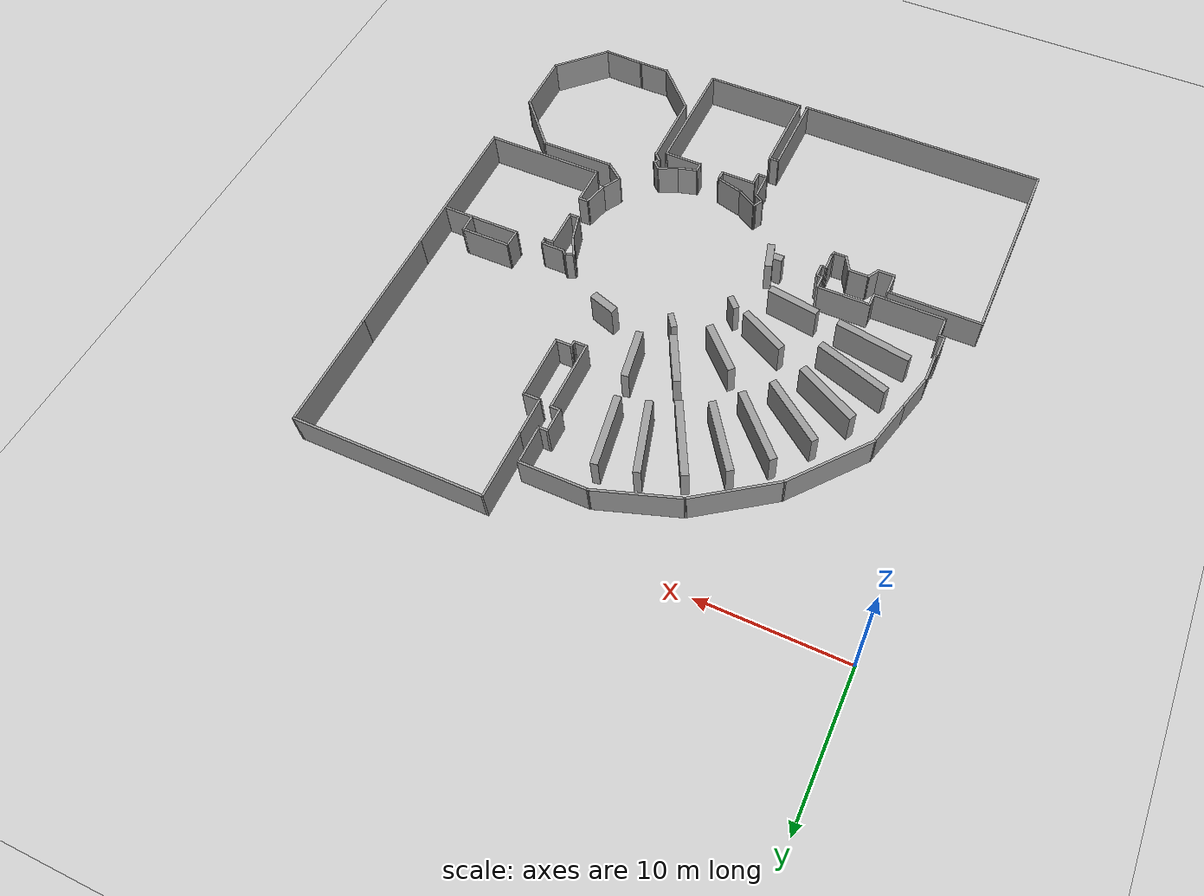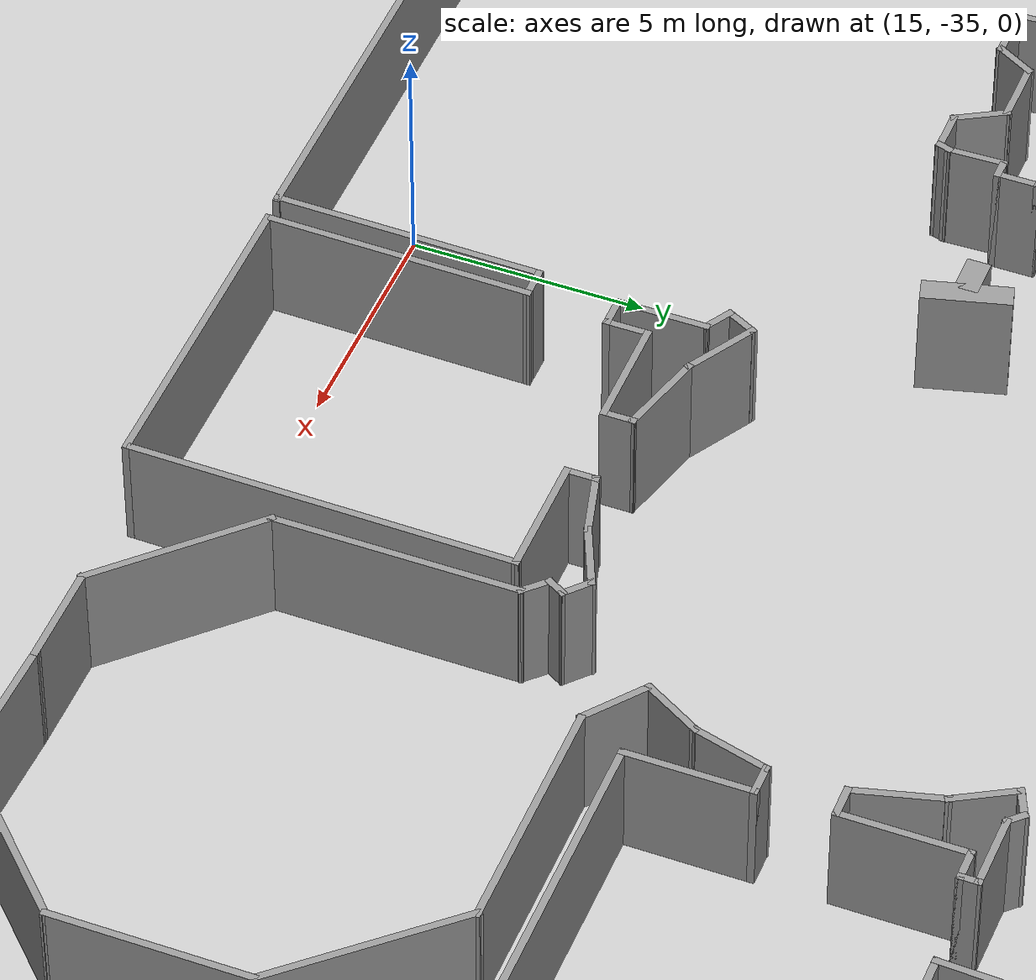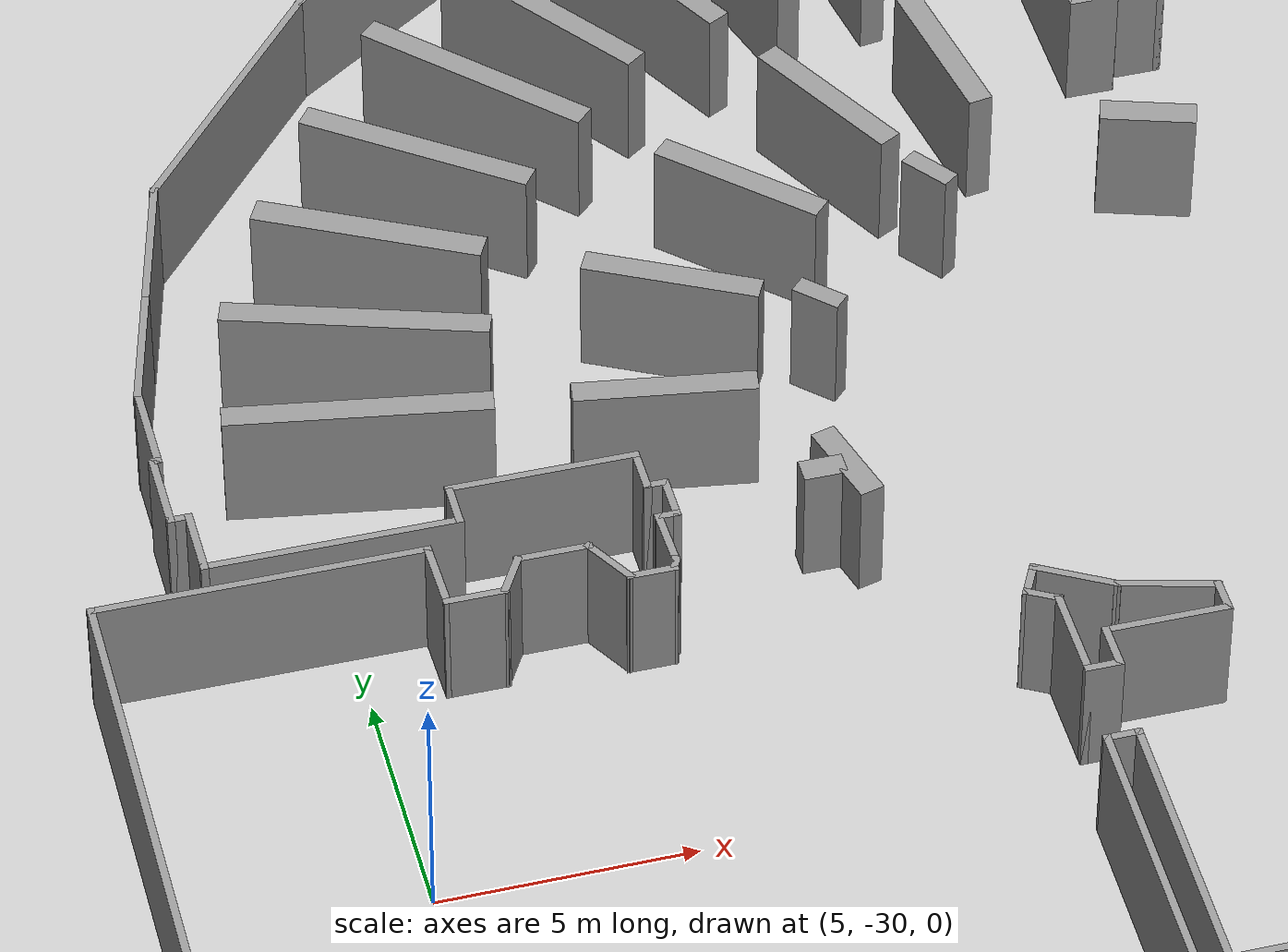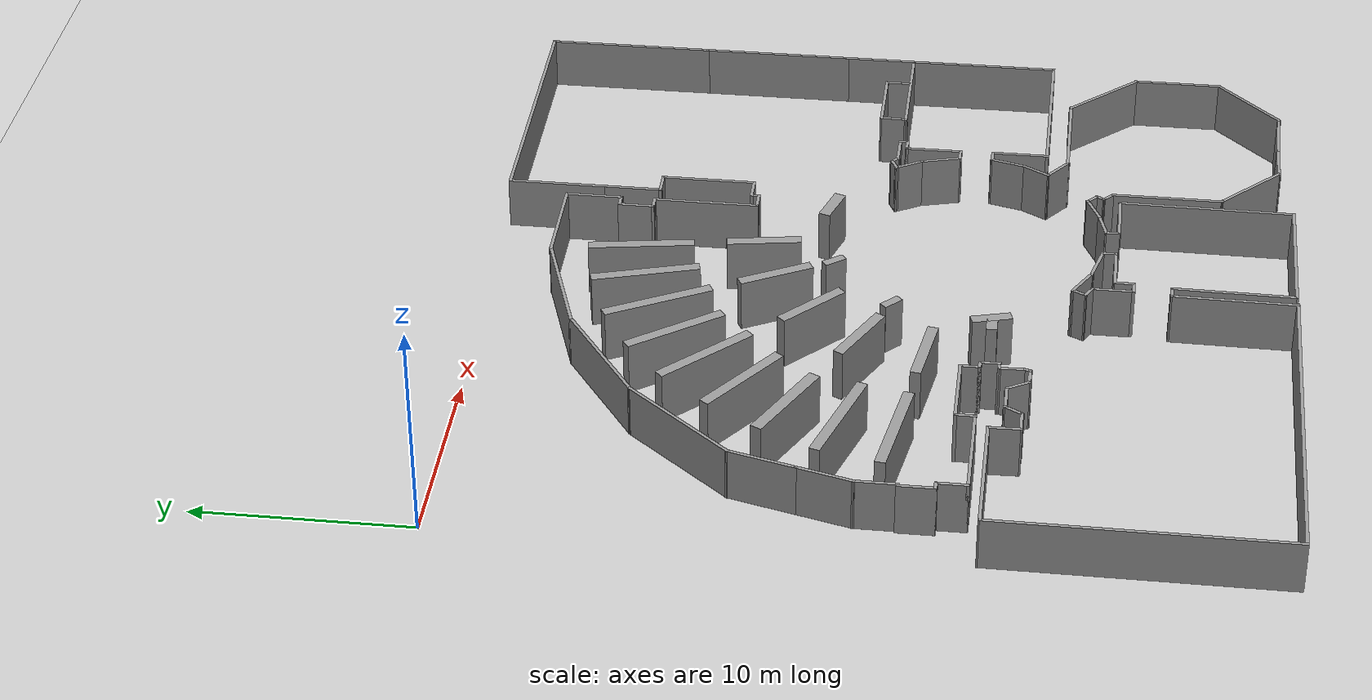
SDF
<sdf version="1.7">
 <world name="default">
  <light name="sun" type="directional">
   <pose>0 0 10 0 -0 0</pose>
   <diffuse>0.8 0.8 0.8 1</diffuse>
   <specular>0.2 0.2 0.2 1</specular>
   <attenuation>
    <range>1000</range>
    <constant>0.9</constant>
    <linear>0.01</linear>
    <quadratic>0.001</quadratic>
   </attenuation>
   <direction>-0.5 0.1 -0.9</direction>
   <spot><inner_angle>0</inner_angle><outer_angle>0</outer_angle><falloff>0</falloff></spot>
  </light>
  <model name="ground_plane">
   <static>1</static>
   <link name="link">
    <collision name="collision">
     <geometry><plane><normal>0 0 1</normal><size>100 100</size></plane></geometry>
     <surface>
      <contact><collide_bitmask>65535</collide_bitmask></contact>
      <friction><ode><mu>100</mu><mu2>50</mu2></ode></friction>
     </surface>
    </collision>
    <visual name="visual">
     <cast_shadows>0</cast_shadows>
     <geometry><plane><normal>0 0 1</normal><size>100 100</size></plane></geometry>
     <material>
      <script><uri>file://media/materials/scripts/gazebo.material</uri><name>Gazebo/Grey</name></script>
     </material>
    </visual>
   </link>
  </model>
  <gravity>0 0 -9.8</gravity>
  <magnetic_field>6e-06 2.3e-05 -4.2e-05</magnetic_field>
  <atmosphere type="adiabatic"/>
  <physics type="ode">
   <max_step_size>0.001</max_step_size>
   <real_time_factor>1</real_time_factor>
   <real_time_update_rate>1000</real_time_update_rate>
  </physics>
  <scene><ambient>0.4 0.4 0.4 1</ambient><background>0.7 0.7 0.7 1</background><shadows>1</shadows></scene>
  <audio><device>default</device></audio>
  <spherical_coordinates>
   <surface_model>EARTH_WGS84</surface_model>
   <latitude_deg>0</latitude_deg>
   <longitude_deg>0</longitude_deg>
   <elevation>0</elevation>
   <heading_deg>0</heading_deg>
  </spherical_coordinates>
  <model name="libraryModel">
   <pose>18.25 -18.5 0 0 -0 0</pose>
   <link name="Wall_1">
    <collision name="Wall_1_Collision">
     <geometry><box><size>6.5 0.15 2.5</size></box></geometry>
     <pose>0 0 1.25 0 -0 0</pose>
    </collision>
    <visual name="Wall_1_Visual">
     <pose>0 0 1.25 0 -0 0</pose>
     <geometry><box><size>6.5 0.15 2.5</size></box></geometry>
     <material>
      <script><uri>file://media/materials/scripts/gazebo.material</uri><name>Gazebo/Grey</name></script>
      <ambient>1 1 1 1</ambient>
     </material>
     <meta><layer>0</layer></meta>
    </visual>
    <pose>-14.9713 -5.1242 0 0 -0 0</pose>
   </link>
   <link name="Wall_10">
    <collision name="Wall_10_Collision">
     <geometry><box><size>1 0.15 2.5</size></box></geometry>
     <pose>0 0 1.25 0 -0 0</pose>
    </collision>
    <visual name="Wall_10_Visual">
     <pose>0 0 1.25 0 -0 0</pose>
     <geometry><box><size>1 0.15 2.5</size></box></geometry>
     <material>
      <script><uri>file://media/materials/scripts/gazebo.material</uri><name>Gazebo/Grey</name></script>
      <ambient>1 1 1 1</ambient>
     </material>
     <meta><layer>0</layer></meta>
    </visual>
    <pose>-7.44635 -4.0992 0 0 -0 1.5708</pose>
   </link>
   <link name="Wall_101">
    <collision name="Wall_101_Collision">
     <geometry><box><size>1.5 0.15 2.5</size></box></geometry>
     <pose>0 0 1.25 0 -0 0</pose>
    </collision>
    <visual name="Wall_101_Visual">
     <pose>0 0 1.25 0 -0 0</pose>
     <geometry><box><size>1.5 0.15 2.5</size></box></geometry>
     <material>
      <script><uri>file://media/materials/scripts/gazebo.material</uri><name>Gazebo/Grey</name></script>
      <ambient>1 1 1 1</ambient>
     </material>
     <meta><layer>0</layer></meta>
    </visual>
    <pose>8.65885 -0.242249 0 0 -0 -1.0472</pose>
   </link>
   <link name="Wall_102">
    <collision name="Wall_102_Collision">
     <geometry><box><size>2 0.15 2.5</size></box></geometry>
     <pose>0 0 1.25 0 -0 0</pose>
    </collision>
    <visual name="Wall_102_Visual">
     <pose>0 0 1.25 0 -0 0</pose>
     <geometry><box><size>2 0.15 2.5</size></box></geometry>
     <material>
      <script><uri>file://media/materials/scripts/gazebo.material</uri><name>Gazebo/Grey</name></script>
      <ambient>1 1 1 1</ambient>
     </material>
     <meta><layer>0</layer></meta>
    </visual>
    <pose>9.23576 -1.7203 0 0 -0 -1.309</pose>
   </link>
   <link name="Wall_103">
    <collision name="Wall_103_Collision">
     <geometry><box><size>0.75 0.15 2.5</size></box></geometry>
     <pose>0 0 1.25 0 -0 0</pose>
    </collision>
    <visual name="Wall_103_Visual">
     <pose>0 0 1.25 0 -0 0</pose>
     <geometry><box><size>0.75 0.15 2.5</size></box></geometry>
     <material>
      <script><uri>file://media/materials/scripts/gazebo.material</uri><name>Gazebo/Grey</name></script>
      <ambient>1 1 1 1</ambient>
     </material>
     <meta><layer>0</layer></meta>
    </visual>
    <pose>9.77517 -2.61378 0 0 -0 0</pose>
   </link>
   <link name="Wall_104">
    <collision name="Wall_104_Collision">
     <geometry><box><size>2.75 0.15 2.5</size></box></geometry>
     <pose>0 0 1.25 0 -0 0</pose>
    </collision>
    <visual name="Wall_104_Visual">
     <pose>0 0 1.25 0 -0 0</pose>
     <geometry><box><size>2.75 0.15 2.5</size></box></geometry>
     <material>
      <script><uri>file://media/materials/scripts/gazebo.material</uri><name>Gazebo/Grey</name></script>
      <ambient>1 1 1 1</ambient>
     </material>
     <meta><layer>0</layer></meta>
    </visual>
    <pose>10.0752 -1.31378 0 0 -0 1.5708</pose>
   </link>
   <link name="Wall_105">
    <collision name="Wall_105_Collision">
     <geometry><box><size>0.75 0.15 2.5</size></box></geometry>
     <pose>0 0 1.25 0 -0 0</pose>
    </collision>
    <visual name="Wall_105_Visual">
     <pose>0 0 1.25 0 -0 0</pose>
     <geometry><box><size>0.75 0.15 2.5</size></box></geometry>
     <material>
      <script><uri>file://media/materials/scripts/gazebo.material</uri><name>Gazebo/Grey</name></script>
      <ambient>1 1 1 1</ambient>
     </material>
     <meta><layer>0</layer></meta>
    </visual>
    <pose>10.3752 -0.013779 0 0 -0 0</pose>
   </link>
   <link name="Wall_106">
    <collision name="Wall_106_Collision">
     <geometry><box><size>0.5 0.15 2.5</size></box></geometry>
     <pose>0 0 1.25 0 -0 0</pose>
    </collision>
    <visual name="Wall_106_Visual">
     <pose>0 0 1.25 0 -0 0</pose>
     <geometry><box><size>0.5 0.15 2.5</size></box></geometry>
     <material>
      <script><uri>file://media/materials/scripts/gazebo.material</uri><name>Gazebo/Grey</name></script>
      <ambient>1 1 1 1</ambient>
     </material>
     <meta><layer>0</layer></meta>
    </visual>
    <pose>10.6752 0.161222 0 0 -0 1.5708</pose>
   </link>
   <link name="Wall_107">
    <collision name="Wall_107_Collision">
     <geometry><box><size>1.71407 0.15 2.5</size></box></geometry>
     <pose>0 0 1.25 0 -0 0</pose>
    </collision>
    <visual name="Wall_107_Visual">
     <pose>0 0 1.25 0 -0 0</pose>
     <geometry><box><size>1.71407 0.15 2.5</size></box></geometry>
     <material>
      <script><uri>file://media/materials/scripts/gazebo.material</uri><name>Gazebo/Grey</name></script>
      <ambient>1 1 1 1</ambient>
     </material>
     <meta><layer>0</layer></meta>
    </visual>
    <pose>9.89314 0.33927 0 0 -0 3.13769</pose>
   </link>
   <link name="Wall_108">
    <collision name="Wall_108_Collision">
     <geometry><box><size>0.5 0.15 2.5</size></box></geometry>
     <pose>0 0 1.25 0 -0 0</pose>
    </collision>
    <visual name="Wall_108_Visual">
     <pose>0 0 1.25 0 -0 0</pose>
     <geometry><box><size>0.5 0.15 2.5</size></box></geometry>
     <material>
      <script><uri>file://media/materials/scripts/gazebo.material</uri><name>Gazebo/Grey</name></script>
      <ambient>1 1 1 1</ambient>
     </material>
     <meta><layer>0</layer></meta>
    </visual>
    <pose>8.98736 0.466062 0 0 -0 2.35619</pose>
   </link>
   <link name="Wall_109">
    <collision name="Wall_109_Collision">
     <geometry><box><size>0.746074 0.15 2.5</size></box></geometry>
     <pose>0 0 1.25 0 -0 0</pose>
    </collision>
    <visual name="Wall_109_Visual">
     <pose>0 0 1.25 0 -0 0</pose>
     <geometry><box><size>0.746074 0.15 2.5</size></box></geometry>
     <material>
      <script><uri>file://media/materials/scripts/gazebo.material</uri><name>Gazebo/Grey</name></script>
      <ambient>1 1 1 1</ambient>
     </material>
     <meta><layer>0</layer></meta>
    </visual>
    <pose>8.59248 0.466062 0 0 -0 -2.71344</pose>
   </link>
   <link name="Wall_11">
    <collision name="Wall_11_Collision">
     <geometry><box><size>3.75 0.15 2.5</size></box></geometry>
     <pose>0 0 1.25 0 -0 0</pose>
    </collision>
    <visual name="Wall_11_Visual">
     <pose>0 0 1.25 0 -0 0</pose>
     <geometry><box><size>3.75 0.15 2.5</size></box></geometry>
     <material>
      <script><uri>file://media/materials/scripts/gazebo.material</uri><name>Gazebo/Grey</name></script>
      <ambient>1 1 1 1</ambient>
     </material>
     <meta><layer>0</layer></meta>
    </visual>
    <pose>-9.24635 -3.6742 0 0 -0 3.14159</pose>
   </link>
   <link name="Wall_111">
    <collision name="Wall_111_Collision">
     <geometry><box><size>5.5 0.15 2.5</size></box></geometry>
     <pose>0 0 1.25 0 -0 0</pose>
    </collision>
    <visual name="Wall_111_Visual">
     <pose>0 0 1.25 0 -0 0</pose>
     <geometry><box><size>5.5 0.15 2.5</size></box></geometry>
     <material>
      <script><uri>file://media/materials/scripts/gazebo.material</uri><name>Gazebo/Grey</name></script>
      <ambient>1 1 1 1</ambient>
     </material>
     <meta><layer>0</layer></meta>
    </visual>
    <pose>15.3789 0.231085 0 0 -0 0</pose>
   </link>
   <link name="Wall_115">
    <collision name="Wall_115_Collision">
     <geometry><box><size>1.8503 0.5 2.5</size></box></geometry>
     <pose>0 0 1.25 0 -0 0</pose>
    </collision>
    <visual name="Wall_115_Visual">
     <pose>0 0 1.25 0 -0 0</pose>
     <geometry><box><size>1.8503 0.5 2.5</size></box></geometry>
     <material>
      <script><uri>file://media/materials/scripts/gazebo.material</uri><name>Gazebo/Grey</name></script>
      <ambient>1 1 1 1</ambient>
     </material>
     <meta><layer>0</layer></meta>
    </visual>
    <pose>-3.6461 -4.83761 0 0 -0 1.83302</pose>
   </link>
   <link name="Wall_117">
    <collision name="Wall_117_Collision">
     <geometry><box><size>0.849678 0.5 2.5</size></box></geometry>
     <pose>0 0 1.25 0 -0 0</pose>
    </collision>
    <visual name="Wall_117_Visual">
     <pose>0 0 1.25 0 -0 0</pose>
     <geometry><box><size>0.849678 0.5 2.5</size></box></geometry>
     <material>
      <script><uri>file://media/materials/scripts/gazebo.material</uri><name>Gazebo/Grey</name></script>
      <ambient>1 1 1 1</ambient>
     </material>
     <meta><layer>0</layer></meta>
    </visual>
    <pose>-4.13511 -4.89061 0 0 -0 0</pose>
   </link>
   <link name="Wall_12">
    <collision name="Wall_12_Collision">
     <geometry><box><size>1 0.15 2.5</size></box></geometry>
     <pose>0 0 1.25 0 -0 0</pose>
    </collision>
    <visual name="Wall_12_Visual">
     <pose>0 0 1.25 0 -0 0</pose>
     <geometry><box><size>1 0.15 2.5</size></box></geometry>
     <material>
      <script><uri>file://media/materials/scripts/gazebo.material</uri><name>Gazebo/Grey</name></script>
      <ambient>1 1 1 1</ambient>
     </material>
     <meta><layer>0</layer></meta>
    </visual>
    <pose>-11.0463 -4.0992 0 0 -0 -1.5708</pose>
   </link>
   <link name="Wall_120">
    <collision name="Wall_120_Collision">
     <geometry><box><size>1.25 0.15 2.5</size></box></geometry>
     <pose>0 0 1.25 0 -0 0</pose>
    </collision>
    <visual name="Wall_120_Visual">
     <pose>0 0 1.25 0 -0 0</pose>
     <geometry><box><size>1.25 0.15 2.5</size></box></geometry>
     <material>
      <script><uri>file://media/materials/scripts/gazebo.material</uri><name>Gazebo/Grey</name></script>
      <ambient>1 1 1 1</ambient>
     </material>
     <meta><layer>0</layer></meta>
    </visual>
    <pose>-11.2176 -6.52441 0 0 -0 0</pose>
   </link>
   <link name="Wall_121">
    <collision name="Wall_121_Collision">
     <geometry><box><size>1 0.15 2.5</size></box></geometry>
     <pose>0 0 1.25 0 -0 0</pose>
    </collision>
    <visual name="Wall_121_Visual">
     <pose>0 0 1.25 0 -0 0</pose>
     <geometry><box><size>1 0.15 2.5</size></box></geometry>
     <material>
      <script><uri>file://media/materials/scripts/gazebo.material</uri><name>Gazebo/Grey</name></script>
      <ambient>1 1 1 1</ambient>
     </material>
     <meta><layer>0</layer></meta>
    </visual>
    <pose>-10.4551 -6.15635 0 0 -0 1.0472</pose>
   </link>
   <link name="Wall_122">
    <collision name="Wall_122_Collision">
     <geometry><box><size>1.5 0.15 2.5</size></box></geometry>
     <pose>0 0 1.25 0 -0 0</pose>
    </collision>
    <visual name="Wall_122_Visual">
     <pose>0 0 1.25 0 -0 0</pose>
     <geometry><box><size>1.5 0.15 2.5</size></box></geometry>
     <material>
      <script><uri>file://media/materials/scripts/gazebo.material</uri><name>Gazebo/Grey</name></script>
      <ambient>1 1 1 1</ambient>
     </material>
     <meta><layer>0</layer></meta>
    </visual>
    <pose>-9.56757 -5.78829 0 0 -0 0</pose>
   </link>
   <link name="Wall_123">
    <collision name="Wall_123_Collision">
     <geometry><box><size>1.25 0.15 2.5</size></box></geometry>
     <pose>0 0 1.25 0 -0 0</pose>
    </collision>
    <visual name="Wall_123_Visual">
     <pose>0 0 1.25 0 -0 0</pose>
     <geometry><box><size>1.25 0.15 2.5</size></box></geometry>
     <material>
      <script><uri>file://media/materials/scripts/gazebo.material</uri><name>Gazebo/Grey</name></script>
      <ambient>1 1 1 1</ambient>
     </material>
     <meta><layer>0</layer></meta>
    </visual>
    <pose>-8.61757 -6.26461 0 0 -0 -1.0472</pose>
   </link>
   <link name="Wall_124">
    <collision name="Wall_124_Collision">
     <geometry><box><size>1 0.15 2.5</size></box></geometry>
     <pose>0 0 1.25 0 -0 0</pose>
    </collision>
    <visual name="Wall_124_Visual">
     <pose>0 0 1.25 0 -0 0</pose>
     <geometry><box><size>1 0.15 2.5</size></box></geometry>
     <material>
      <script><uri>file://media/materials/scripts/gazebo.material</uri><name>Gazebo/Grey</name></script>
      <ambient>1 1 1 1</ambient>
     </material>
     <meta><layer>0</layer></meta>
    </visual>
    <pose>-7.91757 -6.74092 0 0 -0 0</pose>
   </link>
   <link name="Wall_125">
    <collision name="Wall_125_Collision">
     <geometry><box><size>0.379129 0.15 2.5</size></box></geometry>
     <pose>0 0 1.25 0 -0 0</pose>
    </collision>
    <visual name="Wall_125_Visual">
     <pose>0 0 1.25 0 -0 0</pose>
     <geometry><box><size>0.379129 0.15 2.5</size></box></geometry>
     <material>
      <script><uri>file://media/materials/scripts/gazebo.material</uri><name>Gazebo/Grey</name></script>
      <ambient>1 1 1 1</ambient>
     </material>
     <meta><layer>0</layer></meta>
    </visual>
    <pose>-7.45507 -6.63267 0 0 -0 1.23732</pose>
   </link>
   <link name="Wall_127">
    <collision name="Wall_127_Collision">
     <geometry><box><size>5.22507 0.5 2.5</size></box></geometry>
     <pose>0 0 1.25 0 -0 0</pose>
    </collision>
    <visual name="Wall_127_Visual">
     <pose>0 0 1.25 0 -0 0</pose>
     <geometry><box><size>5.22507 0.5 2.5</size></box></geometry>
     <material>
      <script><uri>file://media/materials/scripts/gazebo.material</uri><name>Gazebo/Grey</name></script>
      <ambient>1 1 1 1</ambient>
     </material>
     <meta><layer>0</layer></meta>
    </visual>
    <pose>-3.93287 10.2258 0 0 -0 -1.08254</pose>
   </link>
   <link name="Wall_129">
    <collision name="Wall_129_Collision">
     <geometry><box><size>4.93346 0.5 2.5</size></box></geometry>
     <pose>0 0 1.25 0 -0 0</pose>
    </collision>
    <visual name="Wall_129_Visual">
     <pose>0 0 1.25 0 -0 0</pose>
     <geometry><box><size>4.93346 0.5 2.5</size></box></geometry>
     <material>
      <script><uri>file://media/materials/scripts/gazebo.material</uri><name>Gazebo/Grey</name></script>
      <ambient>1 1 1 1</ambient>
     </material>
     <meta><layer>0</layer></meta>
    </visual>
    <pose>-6.04805 9.1613 0 0 -0 -0.94688</pose>
   </link>
   <link name="Wall_13">
    <collision name="Wall_13_Collision">
     <geometry><box><size>5 0.15 2.5</size></box></geometry>
     <pose>0 0 1.25 0 -0 0</pose>
    </collision>
    <visual name="Wall_13_Visual">
     <pose>0 0 1.25 0 -0 0</pose>
     <geometry><box><size>5 0.15 2.5</size></box></geometry>
     <material>
      <script><uri>file://media/materials/scripts/gazebo.material</uri><name>Gazebo/Grey</name></script>
      <ambient>1 1 1 1</ambient>
     </material>
     <meta><layer>0</layer></meta>
    </visual>
    <pose>-13.4713 -4.5242 0 0 -0 3.14159</pose>
   </link>
   <link name="Wall_131">
    <collision name="Wall_131_Collision">
     <geometry><box><size>5.07999 0.5 2.5</size></box></geometry>
     <pose>0 0 1.25 0 -0 0</pose>
    </collision>
    <visual name="Wall_131_Visual">
     <pose>0 0 1.25 0 -0 0</pose>
     <geometry><box><size>5.07999 0.5 2.5</size></box></geometry>
     <material>
      <script><uri>file://media/materials/scripts/gazebo.material</uri><name>Gazebo/Grey</name></script>
      <ambient>1 1 1 1</ambient>
     </material>
     <meta><layer>0</layer></meta>
    </visual>
    <pose>-7.78959 7.59265 0 0 -0 -0.798745</pose>
   </link>
   <link name="Wall_133">
    <collision name="Wall_133_Collision">
     <geometry><box><size>4.8492 0.5 2.5</size></box></geometry>
     <pose>0 0 1.25 0 -0 0</pose>
    </collision>
    <visual name="Wall_133_Visual">
     <pose>0 0 1.25 0 -0 0</pose>
     <geometry><box><size>4.8492 0.5 2.5</size></box></geometry>
     <material>
      <script><uri>file://media/materials/scripts/gazebo.material</uri><name>Gazebo/Grey</name></script>
      <ambient>1 1 1 1</ambient>
     </material>
     <meta><layer>0</layer></meta>
    </visual>
    <pose>-9.4245 5.75038 0 0 -0 -0.638036</pose>
   </link>
   <link name="Wall_135">
    <collision name="Wall_135_Collision">
     <geometry><box><size>4.61323 0.55 2.5</size></box></geometry>
     <pose>0 0 1.25 0 -0 0</pose>
    </collision>
    <visual name="Wall_135_Visual">
     <pose>0 0 1.25 0 -0 0</pose>
     <geometry><box><size>4.61323 0.55 2.5</size></box></geometry>
     <material>
      <script><uri>file://media/materials/scripts/gazebo.material</uri><name>Gazebo/Grey</name></script>
      <ambient>1 1 1 1</ambient>
     </material>
     <meta><layer>0</layer></meta>
    </visual>
    <pose>-10.8759 3.67924 0 0 -0 2.65712</pose>
   </link>
   <link name="Wall_137">
    <collision name="Wall_137_Collision">
     <geometry><box><size>5.21597 0.5 2.5</size></box></geometry>
     <pose>0 0 1.25 0 -0 0</pose>
    </collision>
    <visual name="Wall_137_Visual">
     <pose>0 0 1.25 0 -0 0</pose>
     <geometry><box><size>5.21597 0.5 2.5</size></box></geometry>
     <material>
      <script><uri>file://media/materials/scripts/gazebo.material</uri><name>Gazebo/Grey</name></script>
      <ambient>1 1 1 1</ambient>
     </material>
     <meta><layer>0</layer></meta>
    </visual>
    <pose>-11.6954 1.29706 0 0 -0 -0.319369</pose>
   </link>
   <link name="Wall_139">
    <collision name="Wall_139_Collision">
     <geometry><box><size>5.16361 0.5 2.5</size></box></geometry>
     <pose>0 0 1.25 0 -0 0</pose>
    </collision>
    <visual name="Wall_139_Visual">
     <pose>0 0 1.25 0 -0 0</pose>
     <geometry><box><size>5.16361 0.5 2.5</size></box></geometry>
     <material>
      <script><uri>file://media/materials/scripts/gazebo.material</uri><name>Gazebo/Grey</name></script>
      <ambient>1 1 1 1</ambient>
     </material>
     <meta><layer>0</layer></meta>
    </visual>
    <pose>-12.2101 -1.15593 0 0 -0 -0.16715</pose>
   </link>
   <link name="Wall_14">
    <collision name="Wall_14_Collision">
     <geometry><box><size>1.5 0.15 2.5</size></box></geometry>
     <pose>0 0 1.25 0 -0 0</pose>
    </collision>
    <visual name="Wall_14_Visual">
     <pose>0 0 1.25 0 -0 0</pose>
     <geometry><box><size>1.5 0.15 2.5</size></box></geometry>
     <material>
      <script><uri>file://media/materials/scripts/gazebo.material</uri><name>Gazebo/Grey</name></script>
      <ambient>1 1 1 1</ambient>
     </material>
     <meta><layer>0</layer></meta>
    </visual>
    <pose>-15.8963 -3.8492 0 0 -0 1.5708</pose>
   </link>
   <link name="Wall_141">
    <collision name="Wall_141_Collision">
     <geometry><box><size>3.55121 0.5 2.5</size></box></geometry>
     <pose>0 0 1.25 0 -0 0</pose>
    </collision>
    <visual name="Wall_141_Visual">
     <pose>0 0 1.25 0 -0 0</pose>
     <geometry><box><size>3.55121 0.5 2.5</size></box></geometry>
     <material>
      <script><uri>file://media/materials/scripts/gazebo.material</uri><name>Gazebo/Grey</name></script>
      <ambient>1 1 1 1</ambient>
     </material>
     <meta><layer>0</layer></meta>
    </visual>
    <pose>-6.4409 -2.02681 0 0 -0 -0.155446</pose>
   </link>
   <link name="Wall_143">
    <collision name="Wall_143_Collision">
     <geometry><box><size>3.51982 0.5 2.5</size></box></geometry>
     <pose>0 0 1.25 0 -0 0</pose>
    </collision>
    <visual name="Wall_143_Visual">
     <pose>0 0 1.25 0 -0 0</pose>
     <geometry><box><size>3.51982 0.5 2.5</size></box></geometry>
     <material>
      <script><uri>file://media/materials/scripts/gazebo.material</uri><name>Gazebo/Grey</name></script>
      <ambient>1 1 1 1</ambient>
     </material>
     <meta><layer>0</layer></meta>
    </visual>
    <pose>-5.51879 0.933116 0 0 -0 -0.483926</pose>
   </link>
   <link name="Wall_145">
    <collision name="Wall_145_Collision">
     <geometry><box><size>3.61835 0.5 2.5</size></box></geometry>
     <pose>0 0 1.25 0 -0 0</pose>
    </collision>
    <visual name="Wall_145_Visual">
     <pose>0 0 1.25 0 -0 0</pose>
     <geometry><box><size>3.61835 0.5 2.5</size></box></geometry>
     <material>
      <script><uri>file://media/materials/scripts/gazebo.material</uri><name>Gazebo/Grey</name></script>
      <ambient>1 1 1 1</ambient>
     </material>
     <meta><layer>0</layer></meta>
    </visual>
    <pose>-3.51427 3.27261 0 0 -0 -0.772674</pose>
   </link>
   <link name="Wall_147">
    <collision name="Wall_147_Collision">
     <geometry><box><size>3.54199 0.5 2.5</size></box></geometry>
     <pose>0 0 1.25 0 -0 0</pose>
    </collision>
    <visual name="Wall_147_Visual">
     <pose>0 0 1.25 0 -0 0</pose>
     <geometry><box><size>3.54199 0.5 2.5</size></box></geometry>
     <material>
      <script><uri>file://media/materials/scripts/gazebo.material</uri><name>Gazebo/Grey</name></script>
      <ambient>1 1 1 1</ambient>
     </material>
     <meta><layer>0</layer></meta>
    </visual>
    <pose>-1.21875 5.15505 0 0 -0 -1.08263</pose>
   </link>
   <link name="Wall_149">
    <collision name="Wall_149_Collision">
     <geometry><box><size>3.46346 0.5 2.5</size></box></geometry>
     <pose>0 0 1.25 0 -0 0</pose>
    </collision>
    <visual name="Wall_149_Visual">
     <pose>0 0 1.25 0 -0 0</pose>
     <geometry><box><size>3.46346 0.5 2.5</size></box></geometry>
     <material>
      <script><uri>file://media/materials/scripts/gazebo.material</uri><name>Gazebo/Grey</name></script>
      <ambient>1 1 1 1</ambient>
     </material>
     <meta><layer>0</layer></meta>
    </visual>
    <pose>1.38052 5.95619 0 0 -0 -1.41247</pose>
   </link>
   <link name="Wall_15">
    <collision name="Wall_15_Collision">
     <geometry><box><size>0.5 0.15 2.5</size></box></geometry>
     <pose>0 0 1.25 0 -0 0</pose>
    </collision>
    <visual name="Wall_15_Visual">
     <pose>0 0 1.25 0 -0 0</pose>
     <geometry><box><size>0.5 0.15 2.5</size></box></geometry>
     <material>
      <script><uri>file://media/materials/scripts/gazebo.material</uri><name>Gazebo/Grey</name></script>
      <ambient>1 1 1 1</ambient>
     </material>
     <meta><layer>0</layer></meta>
    </visual>
    <pose>-16.0713 -3.1742 0 0 -0 3.14159</pose>
   </link>
   <link name="Wall_152">
    <collision name="Wall_152_Collision">
     <geometry><box><size>5.03352 0.5 2.5</size></box></geometry>
     <pose>0 0 1.25 0 -0 0</pose>
    </collision>
    <visual name="Wall_152_Visual">
     <pose>0 0 1.25 0 -0 0</pose>
     <geometry><box><size>5.03352 0.5 2.5</size></box></geometry>
     <material>
      <script><uri>file://media/materials/scripts/gazebo.material</uri><name>Gazebo/Grey</name></script>
      <ambient>1 1 1 1</ambient>
     </material>
     <meta><layer>0</layer></meta>
    </visual>
    <pose>-1.76386 11.0787 0 0 -0 -1.28734</pose>
   </link>
   <link name="Wall_154">
    <collision name="Wall_154_Collision">
     <geometry><box><size>4.92429 0.5 2.5</size></box></geometry>
     <pose>0 0 1.25 0 -0 0</pose>
    </collision>
    <visual name="Wall_154_Visual">
     <pose>0 0 1.25 0 -0 0</pose>
     <geometry><box><size>4.92429 0.5 2.5</size></box></geometry>
     <material>
      <script><uri>file://media/materials/scripts/gazebo.material</uri><name>Gazebo/Grey</name></script>
      <ambient>1 1 1 1</ambient>
     </material>
     <meta><layer>0</layer></meta>
    </visual>
    <pose>0.478676 11.5802 0 0 -0 -1.4162</pose>
   </link>
   <link name="Wall_157">
    <collision name="Wall_157_Collision">
     <geometry><box><size>1.25 0.15 2.5</size></box></geometry>
     <pose>0 0 1.25 0 -0 0</pose>
    </collision>
    <visual name="Wall_157_Visual">
     <pose>0 0 1.25 0 -0 0</pose>
     <geometry><box><size>1.25 0.15 2.5</size></box></geometry>
     <material>
      <script><uri>file://media/materials/scripts/gazebo.material</uri><name>Gazebo/Grey</name></script>
      <ambient>1 1 1 1</ambient>
     </material>
     <meta><layer>0</layer></meta>
    </visual>
    <pose>16.0983 0.865296 0 0 -0 1.5708</pose>
   </link>
   <link name="Wall_158">
    <collision name="Wall_158_Collision">
     <geometry><box><size>3.5 0.15 2.5</size></box></geometry>
     <pose>0 0 1.25 0 -0 0</pose>
    </collision>
    <visual name="Wall_158_Visual">
     <pose>0 0 1.25 0 -0 0</pose>
     <geometry><box><size>3.5 0.15 2.5</size></box></geometry>
     <material>
      <script><uri>file://media/materials/scripts/gazebo.material</uri><name>Gazebo/Grey</name></script>
      <ambient>1 1 1 1</ambient>
     </material>
     <meta><layer>0</layer></meta>
    </visual>
    <pose>14.4233 1.4153 0 0 -0 3.14159</pose>
   </link>
   <link name="Wall_159">
    <collision name="Wall_159_Collision">
     <geometry><box><size>1.33504 0.15 2.5</size></box></geometry>
     <pose>0 0 1.25 0 -0 0</pose>
    </collision>
    <visual name="Wall_159_Visual">
     <pose>0 0 1.25 0 -0 0</pose>
     <geometry><box><size>1.33504 0.15 2.5</size></box></geometry>
     <material>
      <script><uri>file://media/materials/scripts/gazebo.material</uri><name>Gazebo/Grey</name></script>
      <ambient>1 1 1 1</ambient>
     </material>
     <meta><layer>0</layer></meta>
    </visual>
    <pose>12.7261 0.823191 0 0 -0 -1.60824</pose>
   </link>
   <link name="Wall_16">
    <collision name="Wall_16_Collision">
     <geometry><box><size>1.75 0.15 2.5</size></box></geometry>
     <pose>0 0 1.25 0 -0 0</pose>
    </collision>
    <visual name="Wall_16_Visual">
     <pose>0 0 1.25 0 -0 0</pose>
     <geometry><box><size>1.75 0.15 2.5</size></box></geometry>
     <material>
      <script><uri>file://media/materials/scripts/gazebo.material</uri><name>Gazebo/Grey</name></script>
      <ambient>1 1 1 1</ambient>
     </material>
     <meta><layer>0</layer></meta>
    </visual>
    <pose>-16.2463 -2.3742 0 0 -0 1.5708</pose>
   </link>
   <link name="Wall_17">
    <collision name="Wall_17_Collision">
     <geometry><box><size>0.25 0.15 2.5</size></box></geometry>
     <pose>0 0 1.25 0 -0 0</pose>
    </collision>
    <visual name="Wall_17_Visual">
     <pose>0 0 1.25 0 -0 0</pose>
     <geometry><box><size>0.25 0.15 2.5</size></box></geometry>
     <material>
      <script><uri>file://media/materials/scripts/gazebo.material</uri><name>Gazebo/Grey</name></script>
      <ambient>1 1 1 1</ambient>
     </material>
     <meta><layer>0</layer></meta>
    </visual>
    <pose>-16.1963 -1.5742 0 0 -0 0</pose>
   </link>
   <link name="Wall_18">
    <collision name="Wall_18_Collision">
     <geometry><box><size>2 0.15 2.5</size></box></geometry>
     <pose>0 0 1.25 0 -0 0</pose>
    </collision>
    <visual name="Wall_18_Visual">
     <pose>0 0 1.25 0 -0 0</pose>
     <geometry><box><size>2 0.15 2.5</size></box></geometry>
     <material>
      <script><uri>file://media/materials/scripts/gazebo.material</uri><name>Gazebo/Grey</name></script>
      <ambient>1 1 1 1</ambient>
     </material>
     <meta><layer>0</layer></meta>
    </visual>
    <pose>-16.1463 -0.649204 0 0 -0 1.5708</pose>
   </link>
   <link name="Wall_19">
    <collision name="Wall_19_Collision">
     <geometry><box><size>2.75 0.15 2.5</size></box></geometry>
     <pose>0 0 1.25 0 -0 0</pose>
    </collision>
    <visual name="Wall_19_Visual">
     <pose>0 0 1.25 0 -0 0</pose>
     <geometry><box><size>2.75 0.15 2.5</size></box></geometry>
     <material>
      <script><uri>file://media/materials/scripts/gazebo.material</uri><name>Gazebo/Grey</name></script>
      <ambient>1 1 1 1</ambient>
     </material>
     <meta><layer>0</layer></meta>
    </visual>
    <pose>-15.8099 1.5315 0 0 -0 1.309</pose>
   </link>
   <link name="Wall_21">
    <collision name="Wall_21_Collision">
     <geometry><box><size>3.25 0.15 2.5</size></box></geometry>
     <pose>0 0 1.25 0 -0 0</pose>
    </collision>
    <visual name="Wall_21_Visual">
     <pose>0 0 1.25 0 -0 0</pose>
     <geometry><box><size>3.25 0.15 2.5</size></box></geometry>
     <material>
      <script><uri>file://media/materials/scripts/gazebo.material</uri><name>Gazebo/Grey</name></script>
      <ambient>1 1 1 1</ambient>
     </material>
     <meta><layer>0</layer></meta>
    </visual>
    <pose>-15.0723 4.28439 0 0 -0 1.309</pose>
   </link>
   <link name="Wall_22">
    <collision name="Wall_22_Collision">
     <geometry><box><size>6.32238 0.15 2.5</size></box></geometry>
     <pose>0 0 1.25 0 -0 0</pose>
    </collision>
    <visual name="Wall_22_Visual">
     <pose>0 0 1.25 0 -0 0</pose>
     <geometry><box><size>6.32238 0.15 2.5</size></box></geometry>
     <material>
      <script><uri>file://media/materials/scripts/gazebo.material</uri><name>Gazebo/Grey</name></script>
      <ambient>1 1 1 1</ambient>
     </material>
     <meta><layer>0</layer></meta>
    </visual>
    <pose>-12.6884 8.14661 0 0 -0 0.873106</pose>
   </link>
   <link name="Wall_24">
    <collision name="Wall_24_Collision">
     <geometry><box><size>6.12348 0.15 2.5</size></box></geometry>
     <pose>0 0 1.25 0 -0 0</pose>
    </collision>
    <visual name="Wall_24_Visual">
     <pose>0 0 1.25 0 -0 0</pose>
     <geometry><box><size>6.12348 0.15 2.5</size></box></geometry>
     <material>
      <script><uri>file://media/materials/scripts/gazebo.material</uri><name>Gazebo/Grey</name></script>
      <ambient>1 1 1 1</ambient>
     </material>
     <meta><layer>0</layer></meta>
    </visual>
    <pose>-8.24419 12.2034 0 0 -0 0.602142</pose>
   </link>
   <link name="Wall_25">
    <collision name="Wall_25_Collision">
     <geometry><box><size>5.89571 0.15 2.5</size></box></geometry>
     <pose>0 0 1.25 0 -0 0</pose>
    </collision>
    <visual name="Wall_25_Visual">
     <pose>0 0 1.25 0 -0 0</pose>
     <geometry><box><size>5.89571 0.15 2.5</size></box></geometry>
     <material>
      <script><uri>file://media/materials/scripts/gazebo.material</uri><name>Gazebo/Grey</name></script>
      <ambient>1 1 1 1</ambient>
     </material>
     <meta><layer>0</layer></meta>
    </visual>
    <pose>-3.05062 14.7832 0 0 -0 0.314302</pose>
   </link>
   <link name="Wall_26">
    <collision name="Wall_26_Collision">
     <geometry><box><size>4.75 0.15 2.5</size></box></geometry>
     <pose>0 0 1.25 0 -0 0</pose>
    </collision>
    <visual name="Wall_26_Visual">
     <pose>0 0 1.25 0 -0 0</pose>
     <geometry><box><size>4.75 0.15 2.5</size></box></geometry>
     <material>
      <script><uri>file://media/materials/scripts/gazebo.material</uri><name>Gazebo/Grey</name></script>
      <ambient>1 1 1 1</ambient>
     </material>
     <meta><layer>0</layer></meta>
    </visual>
    <pose>1.9817 15.6714 0 0 -0 2e-06</pose>
   </link>
   <link name="Wall_27">
    <collision name="Wall_27_Collision">
     <geometry><box><size>2.75 0.15 2.5</size></box></geometry>
     <pose>0 0 1.25 0 -0 0</pose>
    </collision>
    <visual name="Wall_27_Visual">
     <pose>0 0 1.25 0 -0 0</pose>
     <geometry><box><size>2.75 0.15 2.5</size></box></geometry>
     <material>
      <script><uri>file://media/materials/scripts/gazebo.material</uri><name>Gazebo/Grey</name></script>
      <ambient>1 1 1 1</ambient>
     </material>
     <meta><layer>0</layer></meta>
    </visual>
    <pose>4.28189 14.3714 0 0 -0 -1.5708</pose>
   </link>
   <link name="Wall_28">
    <collision name="Wall_28_Collision">
     <geometry><box><size>0.75 0.15 2.5</size></box></geometry>
     <pose>0 0 1.25 0 -0 0</pose>
    </collision>
    <visual name="Wall_28_Visual">
     <pose>0 0 1.25 0 -0 0</pose>
     <geometry><box><size>0.75 0.15 2.5</size></box></geometry>
     <material>
      <script><uri>file://media/materials/scripts/gazebo.material</uri><name>Gazebo/Grey</name></script>
      <ambient>1 1 1 1</ambient>
     </material>
     <meta><layer>0</layer></meta>
    </visual>
    <pose>3.9817 13.0714 0 0 -0 -3.14158</pose>
   </link>
   <link name="Wall_29">
    <collision name="Wall_29_Collision">
     <geometry><box><size>1.75 0.15 2.5</size></box></geometry>
     <pose>0 0 1.25 0 -0 0</pose>
    </collision>
    <visual name="Wall_29_Visual">
     <pose>0 0 1.25 0 -0 0</pose>
     <geometry><box><size>1.75 0.15 2.5</size></box></geometry>
     <material>
      <script><uri>file://media/materials/scripts/gazebo.material</uri><name>Gazebo/Grey</name></script>
      <ambient>1 1 1 1</ambient>
     </material>
     <meta><layer>0</layer></meta>
    </visual>
    <pose>3.6815 12.2714 0 0 -0 -1.5708</pose>
   </link>
   <link name="Wall_30">
    <collision name="Wall_30_Collision">
     <geometry><box><size>0.75 0.15 2.5</size></box></geometry>
     <pose>0 0 1.25 0 -0 0</pose>
    </collision>
    <visual name="Wall_30_Visual">
     <pose>0 0 1.25 0 -0 0</pose>
     <geometry><box><size>0.75 0.15 2.5</size></box></geometry>
     <material>
      <script><uri>file://media/materials/scripts/gazebo.material</uri><name>Gazebo/Grey</name></script>
      <ambient>1 1 1 1</ambient>
     </material>
     <meta><layer>0</layer></meta>
    </visual>
    <pose>3.9815 11.4714 0 0 -0 0</pose>
   </link>
   <link name="Wall_31">
    <collision name="Wall_31_Collision">
     <geometry><box><size>5 0.15 2.5</size></box></geometry>
     <pose>0 0 1.25 0 -0 0</pose>
    </collision>
    <visual name="Wall_31_Visual">
     <pose>0 0 1.25 0 -0 0</pose>
     <geometry><box><size>5 0.15 2.5</size></box></geometry>
     <material>
      <script><uri>file://media/materials/scripts/gazebo.material</uri><name>Gazebo/Grey</name></script>
      <ambient>1 1 1 1</ambient>
     </material>
     <meta><layer>0</layer></meta>
    </visual>
    <pose>4.2815 9.04638 0 0 -0 -1.5708</pose>
   </link>
   <link name="Wall_33">
    <collision name="Wall_33_Collision">
     <geometry><box><size>1 0.15 2.5</size></box></geometry>
     <pose>0 0 1.25 0 -0 0</pose>
    </collision>
    <visual name="Wall_33_Visual">
     <pose>0 0 1.25 0 -0 0</pose>
     <geometry><box><size>1 0.15 2.5</size></box></geometry>
     <material>
      <script><uri>file://media/materials/scripts/gazebo.material</uri><name>Gazebo/Grey</name></script>
      <ambient>1 1 1 1</ambient>
     </material>
     <meta><layer>0</layer></meta>
    </visual>
    <pose>4.7065 6.62138 0 0 -0 0</pose>
   </link>
   <link name="Wall_34">
    <collision name="Wall_34_Collision">
     <geometry><box><size>0.5 0.15 2.5</size></box></geometry>
     <pose>0 0 1.25 0 -0 0</pose>
    </collision>
    <visual name="Wall_34_Visual">
     <pose>0 0 1.25 0 -0 0</pose>
     <geometry><box><size>0.5 0.15 2.5</size></box></geometry>
     <material>
      <script><uri>file://media/materials/scripts/gazebo.material</uri><name>Gazebo/Grey</name></script>
      <ambient>1 1 1 1</ambient>
     </material>
     <meta><layer>0</layer></meta>
    </visual>
    <pose>5.1315 6.79638 0 0 -0 1.5708</pose>
   </link>
   <link name="Wall_35">
    <collision name="Wall_35_Collision">
     <geometry><box><size>1.25 0.15 2.5</size></box></geometry>
     <pose>0 0 1.25 0 -0 0</pose>
    </collision>
    <visual name="Wall_35_Visual">
     <pose>0 0 1.25 0 -0 0</pose>
     <geometry><box><size>1.25 0.15 2.5</size></box></geometry>
     <material>
      <script><uri>file://media/materials/scripts/gazebo.material</uri><name>Gazebo/Grey</name></script>
      <ambient>1 1 1 1</ambient>
     </material>
     <meta><layer>0</layer></meta>
    </visual>
    <pose>5.6815 6.97138 0 0 -0 0</pose>
   </link>
   <link name="Wall_36">
    <collision name="Wall_36_Collision">
     <geometry><box><size>4.5 0.15 2.5</size></box></geometry>
     <pose>0 0 1.25 0 -0 0</pose>
    </collision>
    <visual name="Wall_36_Visual">
     <pose>0 0 1.25 0 -0 0</pose>
     <geometry><box><size>4.5 0.15 2.5</size></box></geometry>
     <material>
      <script><uri>file://media/materials/scripts/gazebo.material</uri><name>Gazebo/Grey</name></script>
      <ambient>1 1 1 1</ambient>
     </material>
     <meta><layer>0</layer></meta>
    </visual>
    <pose>6.2315 9.14638 0 0 -0 1.5708</pose>
   </link>
   <link name="Wall_37">
    <collision name="Wall_37_Collision">
     <geometry><box><size>1.25 0.15 2.5</size></box></geometry>
     <pose>0 0 1.25 0 -0 0</pose>
    </collision>
    <visual name="Wall_37_Visual">
     <pose>0 0 1.25 0 -0 0</pose>
     <geometry><box><size>1.25 0.15 2.5</size></box></geometry>
     <material>
      <script><uri>file://media/materials/scripts/gazebo.material</uri><name>Gazebo/Grey</name></script>
      <ambient>1 1 1 1</ambient>
     </material>
     <meta><layer>0</layer></meta>
    </visual>
    <pose>5.6815 11.3214 0 0 -0 3.14159</pose>
   </link>
   <link name="Wall_38">
    <collision name="Wall_38_Collision">
     <geometry><box><size>2.75 0.15 2.5</size></box></geometry>
     <pose>0 0 1.25 0 -0 0</pose>
    </collision>
    <visual name="Wall_38_Visual">
     <pose>0 0 1.25 0 -0 0</pose>
     <geometry><box><size>2.75 0.15 2.5</size></box></geometry>
     <material>
      <script><uri>file://media/materials/scripts/gazebo.material</uri><name>Gazebo/Grey</name></script>
      <ambient>1 1 1 1</ambient>
     </material>
     <meta><layer>0</layer></meta>
    </visual>
    <pose>5.1315 12.6214 0 0 -0 1.5708</pose>
   </link>
   <link name="Wall_4">
    <collision name="Wall_4_Collision">
     <geometry><box><size>1.55139 0.15 2.5</size></box></geometry>
     <pose>0 0 1.25 0 -0 0</pose>
    </collision>
    <visual name="Wall_4_Visual">
     <pose>0 0 1.25 0 -0 0</pose>
     <geometry><box><size>1.55139 0.15 2.5</size></box></geometry>
     <material>
      <script><uri>file://media/materials/scripts/gazebo.material</uri><name>Gazebo/Grey</name></script>
      <ambient>1 1 1 1</ambient>
     </material>
     <meta><layer>0</layer></meta>
    </visual>
    <pose>-11.782 -5.82431 0 0 -0 -1.55024</pose>
   </link>
   <link name="Wall_40">
    <collision name="Wall_40_Collision">
     <geometry><box><size>4.75 0.15 2.5</size></box></geometry>
     <pose>0 0 1.25 0 -0 0</pose>
    </collision>
    <visual name="Wall_40_Visual">
     <pose>0 0 1.25 0 -0 0</pose>
     <geometry><box><size>4.75 0.15 2.5</size></box></geometry>
     <material>
      <script><uri>file://media/materials/scripts/gazebo.material</uri><name>Gazebo/Grey</name></script>
      <ambient>1 1 1 1</ambient>
     </material>
     <meta><layer>0</layer></meta>
    </visual>
    <pose>5.1315 16.2214 0 0 -0 1.5708</pose>
   </link>
   <link name="Wall_41">
    <collision name="Wall_41_Collision">
     <geometry><box><size>13.25 0.15 2.5</size></box></geometry>
     <pose>0 0 1.25 0 -0 0</pose>
    </collision>
    <visual name="Wall_41_Visual">
     <pose>0 0 1.25 0 -0 0</pose>
     <geometry><box><size>13.25 0.15 2.5</size></box></geometry>
     <material>
      <script><uri>file://media/materials/scripts/gazebo.material</uri><name>Gazebo/Grey</name></script>
      <ambient>1 1 1 1</ambient>
     </material>
     <meta><layer>0</layer></meta>
    </visual>
    <pose>11.6815 18.5214 0 0 -0 0</pose>
   </link>
   <link name="Wall_42">
    <collision name="Wall_42_Collision">
     <geometry><box><size>8 0.15 2.5</size></box></geometry>
     <pose>0 0 1.25 0 -0 0</pose>
    </collision>
    <visual name="Wall_42_Visual">
     <pose>0 0 1.25 0 -0 0</pose>
     <geometry><box><size>8 0.15 2.5</size></box></geometry>
     <material>
      <script><uri>file://media/materials/scripts/gazebo.material</uri><name>Gazebo/Grey</name></script>
      <ambient>1 1 1 1</ambient>
     </material>
     <meta><layer>0</layer></meta>
    </visual>
    <pose>18.2315 14.5964 0 0 -0 -1.5708</pose>
   </link>
   <link name="Wall_44">
    <collision name="Wall_44_Collision">
     <geometry><box><size>7.25 0.15 2.5</size></box></geometry>
     <pose>0 0 1.25 0 -0 0</pose>
    </collision>
    <visual name="Wall_44_Visual">
     <pose>0 0 1.25 0 -0 0</pose>
     <geometry><box><size>7.25 0.15 2.5</size></box></geometry>
     <material>
      <script><uri>file://media/materials/scripts/gazebo.material</uri><name>Gazebo/Grey</name></script>
      <ambient>1 1 1 1</ambient>
     </material>
     <meta><layer>0</layer></meta>
    </visual>
    <pose>18.2315 7.12138 0 0 -0 -1.5708</pose>
   </link>
   <link name="Wall_47">
    <collision name="Wall_47_Collision">
     <geometry><box><size>10.5 0.15 2.5</size></box></geometry>
     <pose>0 0 1.25 0 -0 0</pose>
    </collision>
    <visual name="Wall_47_Visual">
     <pose>0 0 1.25 0 -0 0</pose>
     <geometry><box><size>10.5 0.15 2.5</size></box></geometry>
     <material>
      <script><uri>file://media/materials/scripts/gazebo.material</uri><name>Gazebo/Grey</name></script>
      <ambient>1 1 1 1</ambient>
     </material>
     <meta><layer>0</layer></meta>
    </visual>
    <pose>18.2315 -1.60362 0 0 -0 -1.5708</pose>
   </link>
   <link name="Wall_48">
    <collision name="Wall_48_Collision">
     <geometry><box><size>8.25 0.15 2.5</size></box></geometry>
     <pose>0 0 1.25 0 -0 0</pose>
    </collision>
    <visual name="Wall_48_Visual">
     <pose>0 0 1.25 0 -0 0</pose>
     <geometry><box><size>8.25 0.15 2.5</size></box></geometry>
     <material>
      <script><uri>file://media/materials/scripts/gazebo.material</uri><name>Gazebo/Grey</name></script>
      <ambient>1 1 1 1</ambient>
     </material>
     <meta><layer>0</layer></meta>
    </visual>
    <pose>14.1815 -6.77862 0 0 -0 3.14159</pose>
   </link>
   <link name="Wall_49">
    <collision name="Wall_49_Collision">
     <geometry><box><size>2.75 0.15 2.5</size></box></geometry>
     <pose>0 0 1.25 0 -0 0</pose>
    </collision>
    <visual name="Wall_49_Visual">
     <pose>0 0 1.25 0 -0 0</pose>
     <geometry><box><size>2.75 0.15 2.5</size></box></geometry>
     <material>
      <script><uri>file://media/materials/scripts/gazebo.material</uri><name>Gazebo/Grey</name></script>
      <ambient>1 1 1 1</ambient>
     </material>
     <meta><layer>0</layer></meta>
    </visual>
    <pose>10.1315 -5.47862 0 0 -0 1.5708</pose>
   </link>
   <link name="Wall_50">
    <collision name="Wall_50_Collision">
     <geometry><box><size>0.75 0.15 2.5</size></box></geometry>
     <pose>0 0 1.25 0 -0 0</pose>
    </collision>
    <visual name="Wall_50_Visual">
     <pose>0 0 1.25 0 -0 0</pose>
     <geometry><box><size>0.75 0.15 2.5</size></box></geometry>
     <material>
      <script><uri>file://media/materials/scripts/gazebo.material</uri><name>Gazebo/Grey</name></script>
      <ambient>1 1 1 1</ambient>
     </material>
     <meta><layer>0</layer></meta>
    </visual>
    <pose>9.8315 -4.17862 0 0 -0 3.14159</pose>
   </link>
   <link name="Wall_51">
    <collision name="Wall_51_Collision">
     <geometry><box><size>1.75 0.15 2.5</size></box></geometry>
     <pose>0 0 1.25 0 -0 0</pose>
    </collision>
    <visual name="Wall_51_Visual">
     <pose>0 0 1.25 0 -0 0</pose>
     <geometry><box><size>1.75 0.15 2.5</size></box></geometry>
     <material>
      <script><uri>file://media/materials/scripts/gazebo.material</uri><name>Gazebo/Grey</name></script>
      <ambient>1 1 1 1</ambient>
     </material>
     <meta><layer>0</layer></meta>
    </visual>
    <pose>9.32444 -4.95136 0 0 -0 -1.8326</pose>
   </link>
   <link name="Wall_52">
    <collision name="Wall_52_Collision">
     <geometry><box><size>1.5 0.15 2.5</size></box></geometry>
     <pose>0 0 1.25 0 -0 0</pose>
    </collision>
    <visual name="Wall_52_Visual">
     <pose>0 0 1.25 0 -0 0</pose>
     <geometry><box><size>1.5 0.15 2.5</size></box></geometry>
     <material>
      <script><uri>file://media/materials/scripts/gazebo.material</uri><name>Gazebo/Grey</name></script>
      <ambient>1 1 1 1</ambient>
     </material>
     <meta><layer>0</layer></meta>
    </visual>
    <pose>8.77989 -6.30867 0 0 -0 -2.0944</pose>
   </link>
   <link name="Wall_53">
    <collision name="Wall_53_Collision">
     <geometry><box><size>1.61327 0.15 2.5</size></box></geometry>
     <pose>0 0 1.25 0 -0 0</pose>
    </collision>
    <visual name="Wall_53_Visual">
     <pose>0 0 1.25 0 -0 0</pose>
     <geometry><box><size>1.61327 0.15 2.5</size></box></geometry>
     <material>
      <script><uri>file://media/materials/scripts/gazebo.material</uri><name>Gazebo/Grey</name></script>
      <ambient>1 1 1 1</ambient>
     </material>
     <meta><layer>0</layer></meta>
    </visual>
    <pose>9.02042 -7.34175 0 0 -0 -0.659894</pose>
   </link>
   <link name="Wall_54">
    <collision name="Wall_54_Collision">
     <geometry><box><size>5.25 0.15 2.5</size></box></geometry>
     <pose>0 0 1.25 0 -0 0</pose>
    </collision>
    <visual name="Wall_54_Visual">
     <pose>0 0 1.25 0 -0 0</pose>
     <geometry><box><size>5.25 0.15 2.5</size></box></geometry>
     <material>
      <script><uri>file://media/materials/scripts/gazebo.material</uri><name>Gazebo/Grey</name></script>
      <ambient>1 1 1 1</ambient>
     </material>
     <meta><layer>0</layer></meta>
    </visual>
    <pose>12.1772 -7.79027 0 0 -0 0</pose>
   </link>
   <link name="Wall_55">
    <collision name="Wall_55_Collision">
     <geometry><box><size>4.40219 0.15 2.5</size></box></geometry>
     <pose>0 0 1.25 0 -0 0</pose>
    </collision>
    <visual name="Wall_55_Visual">
     <pose>0 0 1.25 0 -0 0</pose>
     <geometry><box><size>4.40219 0.15 2.5</size></box></geometry>
     <material>
      <script><uri>file://media/materials/scripts/gazebo.material</uri><name>Gazebo/Grey</name></script>
      <ambient>1 1 1 1</ambient>
     </material>
     <meta><layer>0</layer></meta>
    </visual>
    <pose>16.1357 -9.35701 0 0 -0 -0.828487</pose>
   </link>
   <link name="Wall_56">
    <collision name="Wall_56_Collision">
     <geometry><box><size>4.25 0.15 2.5</size></box></geometry>
     <pose>0 0 1.25 0 -0 0</pose>
    </collision>
    <visual name="Wall_56_Visual">
     <pose>0 0 1.25 0 -0 0</pose>
     <geometry><box><size>4.25 0.15 2.5</size></box></geometry>
     <material>
      <script><uri>file://media/materials/scripts/gazebo.material</uri><name>Gazebo/Grey</name></script>
      <ambient>1 1 1 1</ambient>
     </material>
     <meta><layer>0</layer></meta>
    </visual>
    <pose>17.5729 -12.9737 0 0 -0 -1.5708</pose>
   </link>
   <link name="Wall_6">
    <collision name="Wall_6_Collision">
     <geometry><box><size>1.30057 0.15 2.5</size></box></geometry>
     <pose>0 0 1.25 0 -0 0</pose>
    </collision>
    <visual name="Wall_6_Visual">
     <pose>0 0 1.25 0 -0 0</pose>
     <geometry><box><size>1.30057 0.15 2.5</size></box></geometry>
     <material>
      <script><uri>file://media/materials/scripts/gazebo.material</uri><name>Gazebo/Grey</name></script>
      <ambient>1 1 1 1</ambient>
     </material>
     <meta><layer>0</layer></meta>
    </visual>
    <pose>-7.43196 -5.94931 0 0 -0 1.59581</pose>
   </link>
   <link name="Wall_60">
    <collision name="Wall_60_Collision">
     <geometry><box><size>13.5464 0.15 2.5</size></box></geometry>
     <pose>0 0 1.25 0 -0 0</pose>
    </collision>
    <visual name="Wall_60_Visual">
     <pose>0 0 1.25 0 -0 0</pose>
     <geometry><box><size>13.5464 0.15 2.5</size></box></geometry>
     <material>
      <script><uri>file://media/materials/scripts/gazebo.material</uri><name>Gazebo/Grey</name></script>
      <ambient>1 1 1 1</ambient>
     </material>
     <meta><layer>0</layer></meta>
    </visual>
    <pose>-18.1887 -11.8224 0 0 -0 -1.57712</pose>
   </link>
   <link name="Wall_61">
    <collision name="Wall_61_Collision">
     <geometry><box><size>17.25 0.15 2.5</size></box></geometry>
     <pose>0 0 1.25 0 -0 0</pose>
    </collision>
    <visual name="Wall_61_Visual">
     <pose>0 0 1.25 0 -0 0</pose>
     <geometry><box><size>17.25 0.15 2.5</size></box></geometry>
     <material>
      <script><uri>file://media/materials/scripts/gazebo.material</uri><name>Gazebo/Grey</name></script>
      <ambient>1 1 1 1</ambient>
     </material>
     <meta><layer>0</layer></meta>
    </visual>
    <pose>-9.63869 -18.5206 0 0 -0 0</pose>
   </link>
   <link name="Wall_62">
    <collision name="Wall_62_Collision">
     <geometry><box><size>5.79638 0.15 2.5</size></box></geometry>
     <pose>0 0 1.25 0 -0 0</pose>
    </collision>
    <visual name="Wall_62_Visual">
     <pose>0 0 1.25 0 -0 0</pose>
     <geometry><box><size>5.79638 0.15 2.5</size></box></geometry>
     <material>
      <script><uri>file://media/materials/scripts/gazebo.material</uri><name>Gazebo/Grey</name></script>
      <ambient>1 1 1 1</ambient>
     </material>
     <meta><layer>0</layer></meta>
    </visual>
    <pose>-1.08869 -15.6974 0 0 -0 1.5558</pose>
   </link>
   <link name="Wall_63">
    <collision name="Wall_63_Collision">
     <geometry><box><size>0.75 0.15 2.5</size></box></geometry>
     <pose>0 0 1.25 0 -0 0</pose>
    </collision>
    <visual name="Wall_63_Visual">
     <pose>0 0 1.25 0 -0 0</pose>
     <geometry><box><size>0.75 0.15 2.5</size></box></geometry>
     <material>
      <script><uri>file://media/materials/scripts/gazebo.material</uri><name>Gazebo/Grey</name></script>
      <ambient>1 1 1 1</ambient>
     </material>
     <meta><layer>0</layer></meta>
    </visual>
    <pose>-0.746349 -12.8742 0 0 -0 0</pose>
   </link>
   <link name="Wall_64">
    <collision name="Wall_64_Collision">
     <geometry><box><size>5.67001 0.15 2.5</size></box></geometry>
     <pose>0 0 1.25 0 -0 0</pose>
    </collision>
    <visual name="Wall_64_Visual">
     <pose>0 0 1.25 0 -0 0</pose>
     <geometry><box><size>5.67001 0.15 2.5</size></box></geometry>
     <material>
      <script><uri>file://media/materials/scripts/gazebo.material</uri><name>Gazebo/Grey</name></script>
      <ambient>1 1 1 1</ambient>
     </material>
     <meta><layer>0</layer></meta>
    </visual>
    <pose>-0.488688 -15.6339 0 0 -0 -1.58614</pose>
   </link>
   <link name="Wall_65">
    <collision name="Wall_65_Collision">
     <geometry><box><size>7 0.15 2.5</size></box></geometry>
     <pose>0 0 1.25 0 -0 0</pose>
    </collision>
    <visual name="Wall_65_Visual">
     <pose>0 0 1.25 0 -0 0</pose>
     <geometry><box><size>7 0.15 2.5</size></box></geometry>
     <material>
      <script><uri>file://media/materials/scripts/gazebo.material</uri><name>Gazebo/Grey</name></script>
      <ambient>1 1 1 1</ambient>
     </material>
     <meta><layer>0</layer></meta>
    </visual>
    <pose>2.89397 -18.4782 0 0 -0 0</pose>
   </link>
   <link name="Wall_66">
    <collision name="Wall_66_Collision">
     <geometry><box><size>8.1698 0.15 2.5</size></box></geometry>
     <pose>0 0 1.25 0 -0 0</pose>
    </collision>
    <visual name="Wall_66_Visual">
     <pose>0 0 1.25 0 -0 0</pose>
     <geometry><box><size>8.1698 0.15 2.5</size></box></geometry>
     <material>
      <script><uri>file://media/materials/scripts/gazebo.material</uri><name>Gazebo/Grey</name></script>
      <ambient>1 1 1 1</ambient>
     </material>
     <meta><layer>0</layer></meta>
    </visual>
    <pose>6.36131 -14.3839 0 0 -0 1.56024</pose>
   </link>
   <link name="Wall_67">
    <collision name="Wall_67_Collision">
     <geometry><box><size>2.75 0.15 2.5</size></box></geometry>
     <pose>0 0 1.25 0 -0 0</pose>
    </collision>
    <visual name="Wall_67_Visual">
     <pose>0 0 1.25 0 -0 0</pose>
     <geometry><box><size>2.75 0.15 2.5</size></box></geometry>
     <material>
      <script><uri>file://media/materials/scripts/gazebo.material</uri><name>Gazebo/Grey</name></script>
      <ambient>1 1 1 1</ambient>
     </material>
     <meta><layer>0</layer></meta>
    </visual>
    <pose>5.10365 -10.3742 0 0 -0 3.14159</pose>
   </link>
   <link name="Wall_68">
    <collision name="Wall_68_Collision">
     <geometry><box><size>0.75 0.15 2.5</size></box></geometry>
     <pose>0 0 1.25 0 -0 0</pose>
    </collision>
    <visual name="Wall_68_Visual">
     <pose>0 0 1.25 0 -0 0</pose>
     <geometry><box><size>0.75 0.15 2.5</size></box></geometry>
     <material>
      <script><uri>file://media/materials/scripts/gazebo.material</uri><name>Gazebo/Grey</name></script>
      <ambient>1 1 1 1</ambient>
     </material>
     <meta><layer>0</layer></meta>
    </visual>
    <pose>3.80365 -10.0742 0 0 -0 1.5708</pose>
   </link>
   <link name="Wall_69">
    <collision name="Wall_69_Collision">
     <geometry><box><size>1.5 0.15 2.5</size></box></geometry>
     <pose>0 0 1.25 0 -0 0</pose>
    </collision>
    <visual name="Wall_69_Visual">
     <pose>0 0 1.25 0 -0 0</pose>
     <geometry><box><size>1.5 0.15 2.5</size></box></geometry>
     <material>
      <script><uri>file://media/materials/scripts/gazebo.material</uri><name>Gazebo/Grey</name></script>
      <ambient>1 1 1 1</ambient>
     </material>
     <meta><layer>0</layer></meta>
    </visual>
    <pose>4.45565 -9.5995 0 0 -0 0.261799</pose>
   </link>
   <link name="Wall_7">
    <collision name="Wall_7_Collision">
     <geometry><box><size>0.5 0.15 2.5</size></box></geometry>
     <pose>0 0 1.25 0 -0 0</pose>
    </collision>
    <visual name="Wall_7_Visual">
     <pose>0 0 1.25 0 -0 0</pose>
     <geometry><box><size>0.5 0.15 2.5</size></box></geometry>
     <material>
      <script><uri>file://media/materials/scripts/gazebo.material</uri><name>Gazebo/Grey</name></script>
      <ambient>1 1 1 1</ambient>
     </material>
     <meta><layer>0</layer></meta>
    </visual>
    <pose>-7.27135 -5.3742 0 0 -0 0</pose>
   </link>
   <link name="Wall_70">
    <collision name="Wall_70_Collision">
     <geometry><box><size>1.5296 0.15 2.5</size></box></geometry>
     <pose>0 0 1.25 0 -0 0</pose>
    </collision>
    <visual name="Wall_70_Visual">
     <pose>0 0 1.25 0 -0 0</pose>
     <geometry><box><size>1.5296 0.15 2.5</size></box></geometry>
     <material>
      <script><uri>file://media/materials/scripts/gazebo.material</uri><name>Gazebo/Grey</name></script>
      <ambient>1 1 1 1</ambient>
     </material>
     <meta><layer>0</layer></meta>
    </visual>
    <pose>5.73685 -9.14208 0 0 -0 0.422303</pose>
   </link>
   <link name="Wall_71">
    <collision name="Wall_71_Collision">
     <geometry><box><size>0.755789 0.15 2.5</size></box></geometry>
     <pose>0 0 1.25 0 -0 0</pose>
    </collision>
    <visual name="Wall_71_Visual">
     <pose>0 0 1.25 0 -0 0</pose>
     <geometry><box><size>0.755789 0.15 2.5</size></box></geometry>
     <material>
      <script><uri>file://media/materials/scripts/gazebo.material</uri><name>Gazebo/Grey</name></script>
      <ambient>1 1 1 1</ambient>
     </material>
     <meta><layer>0</layer></meta>
    </visual>
    <pose>6.59551 -9.06168 0 0 -0 -0.731509</pose>
   </link>
   <link name="Wall_72">
    <collision name="Wall_72_Collision">
     <geometry><box><size>0.534818 0.15 2.5</size></box></geometry>
     <pose>0 0 1.25 0 -0 0</pose>
    </collision>
    <visual name="Wall_72_Visual">
     <pose>0 0 1.25 0 -0 0</pose>
     <geometry><box><size>0.534818 0.15 2.5</size></box></geometry>
     <material>
      <script><uri>file://media/materials/scripts/gazebo.material</uri><name>Gazebo/Grey</name></script>
      <ambient>1 1 1 1</ambient>
     </material>
     <meta><layer>0</layer></meta>
    </visual>
    <pose>6.72563 -9.43117 0 0 -0 -2.08891</pose>
   </link>
   <link name="Wall_73">
    <collision name="Wall_73_Collision">
     <geometry><box><size>0.75 0.15 2.5</size></box></geometry>
     <pose>0 0 1.25 0 -0 0</pose>
    </collision>
    <visual name="Wall_73_Visual">
     <pose>0 0 1.25 0 -0 0</pose>
     <geometry><box><size>0.75 0.15 2.5</size></box></geometry>
     <material>
      <script><uri>file://media/materials/scripts/gazebo.material</uri><name>Gazebo/Grey</name></script>
      <ambient>1 1 1 1</ambient>
     </material>
     <meta><layer>0</layer></meta>
    </visual>
    <pose>6.84247 -9.81046 0 0 -0 -0.785398</pose>
   </link>
   <link name="Wall_74">
    <collision name="Wall_74_Collision">
     <geometry><box><size>5.25 0.15 2.5</size></box></geometry>
     <pose>0 0 1.25 0 -0 0</pose>
    </collision>
    <visual name="Wall_74_Visual">
     <pose>0 0 1.25 0 -0 0</pose>
     <geometry><box><size>5.25 0.15 2.5</size></box></geometry>
     <material>
      <script><uri>file://media/materials/scripts/gazebo.material</uri><name>Gazebo/Grey</name></script>
      <ambient>1 1 1 1</ambient>
     </material>
     <meta><layer>0</layer></meta>
    </visual>
    <pose>7.0546 -12.5726 0 0 -0 -1.5708</pose>
   </link>
   <link name="Wall_75">
    <collision name="Wall_75_Collision">
     <geometry><box><size>4 0.15 2.5</size></box></geometry>
     <pose>0 0 1.25 0 -0 0</pose>
    </collision>
    <visual name="Wall_75_Visual">
     <pose>0 0 1.25 0 -0 0</pose>
     <geometry><box><size>4 0.15 2.5</size></box></geometry>
     <material>
      <script><uri>file://media/materials/scripts/gazebo.material</uri><name>Gazebo/Grey</name></script>
      <ambient>1 1 1 1</ambient>
     </material>
     <meta><layer>0</layer></meta>
    </visual>
    <pose>8.41578 -16.4838 0 0 -0 -0.785398</pose>
   </link>
   <link name="Wall_76">
    <collision name="Wall_76_Collision">
     <geometry><box><size>2.25 0.15 2.5</size></box></geometry>
     <pose>0 0 1.25 0 -0 0</pose>
    </collision>
    <visual name="Wall_76_Visual">
     <pose>0 0 1.25 0 -0 0</pose>
     <geometry><box><size>2.25 0.15 2.5</size></box></geometry>
     <material>
      <script><uri>file://media/materials/scripts/gazebo.material</uri><name>Gazebo/Grey</name></script>
      <ambient>1 1 1 1</ambient>
     </material>
     <meta><layer>0</layer></meta>
    </visual>
    <pose>10.827 -17.845 0 0 -0 0</pose>
   </link>
   <link name="Wall_78">
    <collision name="Wall_78_Collision">
     <geometry><box><size>2.94788 0.15 2.5</size></box></geometry>
     <pose>0 0 1.25 0 -0 0</pose>
    </collision>
    <visual name="Wall_78_Visual">
     <pose>0 0 1.25 0 -0 0</pose>
     <geometry><box><size>2.94788 0.15 2.5</size></box></geometry>
     <material>
      <script><uri>file://media/materials/scripts/gazebo.material</uri><name>Gazebo/Grey</name></script>
      <ambient>1 1 1 1</ambient>
     </material>
     <meta><layer>0</layer></meta>
    </visual>
    <pose>13.2754 -17.8839 0 0 -0 -0.027858</pose>
   </link>
   <link name="Wall_79">
    <collision name="Wall_79_Collision">
     <geometry><box><size>4.25 0.15 2.5</size></box></geometry>
     <pose>0 0 1.25 0 -0 0</pose>
    </collision>
    <visual name="Wall_79_Visual">
     <pose>0 0 1.25 0 -0 0</pose>
     <geometry><box><size>4.25 0.15 2.5</size></box></geometry>
     <material>
      <script><uri>file://media/materials/scripts/gazebo.material</uri><name>Gazebo/Grey</name></script>
      <ambient>1 1 1 1</ambient>
     </material>
     <meta><layer>0</layer></meta>
    </visual>
    <pose>16.1233 -16.4733 0 0 -0 0.785398</pose>
   </link>
   <link name="Wall_8">
    <collision name="Wall_8_Collision">
     <geometry><box><size>1 0.15 2.5</size></box></geometry>
     <pose>0 0 1.25 0 -0 0</pose>
    </collision>
    <visual name="Wall_8_Visual">
     <pose>0 0 1.25 0 -0 0</pose>
     <geometry><box><size>1 0.15 2.5</size></box></geometry>
     <material>
      <script><uri>file://media/materials/scripts/gazebo.material</uri><name>Gazebo/Grey</name></script>
      <ambient>1 1 1 1</ambient>
     </material>
     <meta><layer>0</layer></meta>
    </visual>
    <pose>-7.09635 -4.9492 0 0 -0 1.5708</pose>
   </link>
   <link name="Wall_81">
    <collision name="Wall_81_Collision">
     <geometry><box><size>1.75 0.15 2.5</size></box></geometry>
     <pose>0 0 1.25 0 -0 0</pose>
    </collision>
    <visual name="Wall_81_Visual">
     <pose>0 0 1.25 0 -0 0</pose>
     <geometry><box><size>1.75 0.15 2.5</size></box></geometry>
     <material>
      <script><uri>file://media/materials/scripts/gazebo.material</uri><name>Gazebo/Grey</name></script>
      <ambient>1 1 1 1</ambient>
     </material>
     <meta><layer>0</layer></meta>
    </visual>
    <pose>-0.394268 -8.79697 0 0 -0 -0.523599</pose>
   </link>
   <link name="Wall_82">
    <collision name="Wall_82_Collision">
     <geometry><box><size>2 0.15 2.5</size></box></geometry>
     <pose>0 0 1.25 0 -0 0</pose>
    </collision>
    <visual name="Wall_82_Visual">
     <pose>0 0 1.25 0 -0 0</pose>
     <geometry><box><size>2 0.15 2.5</size></box></geometry>
     <material>
      <script><uri>file://media/materials/scripts/gazebo.material</uri><name>Gazebo/Grey</name></script>
      <ambient>1 1 1 1</ambient>
     </material>
     <meta><layer>0</layer></meta>
    </visual>
    <pose>1.19203 -9.43638 0 0 -0 -0.261799</pose>
   </link>
   <link name="Wall_83">
    <collision name="Wall_83_Collision">
     <geometry><box><size>0.75 0.15 2.5</size></box></geometry>
     <pose>0 0 1.25 0 -0 0</pose>
    </collision>
    <visual name="Wall_83_Visual">
     <pose>0 0 1.25 0 -0 0</pose>
     <geometry><box><size>0.75 0.15 2.5</size></box></geometry>
     <material>
      <script><uri>file://media/materials/scripts/gazebo.material</uri><name>Gazebo/Grey</name></script>
      <ambient>1 1 1 1</ambient>
     </material>
     <meta><layer>0</layer></meta>
    </visual>
    <pose>2.08552 -9.97578 0 0 -0 -1.5708</pose>
   </link>
   <link name="Wall_84">
    <collision name="Wall_84_Collision">
     <geometry><box><size>2.5 0.15 2.5</size></box></geometry>
     <pose>0 0 1.25 0 -0 0</pose>
    </collision>
    <visual name="Wall_84_Visual">
     <pose>0 0 1.25 0 -0 0</pose>
     <geometry><box><size>2.5 0.15 2.5</size></box></geometry>
     <material>
      <script><uri>file://media/materials/scripts/gazebo.material</uri><name>Gazebo/Grey</name></script>
      <ambient>1 1 1 1</ambient>
     </material>
     <meta><layer>0</layer></meta>
    </visual>
    <pose>0.910515 -10.2758 0 0 -0 3.14159</pose>
   </link>
   <link name="Wall_85">
    <collision name="Wall_85_Collision">
     <geometry><box><size>1 0.15 2.5</size></box></geometry>
     <pose>0 0 1.25 0 -0 0</pose>
    </collision>
    <visual name="Wall_85_Visual">
     <pose>0 0 1.25 0 -0 0</pose>
     <geometry><box><size>1 0.15 2.5</size></box></geometry>
     <material>
      <script><uri>file://media/materials/scripts/gazebo.material</uri><name>Gazebo/Grey</name></script>
      <ambient>1 1 1 1</ambient>
     </material>
     <meta><layer>0</layer></meta>
    </visual>
    <pose>-0.264485 -10.7008 0 0 -0 -1.5708</pose>
   </link>
   <link name="Wall_86">
    <collision name="Wall_86_Collision">
     <geometry><box><size>0.75 0.15 2.5</size></box></geometry>
     <pose>0 0 1.25 0 -0 0</pose>
    </collision>
    <visual name="Wall_86_Visual">
     <pose>0 0 1.25 0 -0 0</pose>
     <geometry><box><size>0.75 0.15 2.5</size></box></geometry>
     <material>
      <script><uri>file://media/materials/scripts/gazebo.material</uri><name>Gazebo/Grey</name></script>
      <ambient>1 1 1 1</ambient>
     </material>
     <meta><layer>0</layer></meta>
    </visual>
    <pose>-0.564485 -11.1258 0 0 -0 3.14159</pose>
   </link>
   <link name="Wall_87">
    <collision name="Wall_87_Collision">
     <geometry><box><size>2 0.15 2.5</size></box></geometry>
     <pose>0 0 1.25 0 -0 0</pose>
    </collision>
    <visual name="Wall_87_Visual">
     <pose>0 0 1.25 0 -0 0</pose>
     <geometry><box><size>2 0.15 2.5</size></box></geometry>
     <material>
      <script><uri>file://media/materials/scripts/gazebo.material</uri><name>Gazebo/Grey</name></script>
      <ambient>1 1 1 1</ambient>
     </material>
     <meta><layer>0</layer></meta>
    </visual>
    <pose>-0.864485 -10.2008 0 0 -0 1.5708</pose>
   </link>
   <link name="Wall_88">
    <collision name="Wall_88_Collision">
     <geometry><box><size>0.75 0.15 2.5</size></box></geometry>
     <pose>0 0 1.25 0 -0 0</pose>
    </collision>
    <visual name="Wall_88_Visual">
     <pose>0 0 1.25 0 -0 0</pose>
     <geometry><box><size>0.75 0.15 2.5</size></box></geometry>
     <material>
      <script><uri>file://media/materials/scripts/gazebo.material</uri><name>Gazebo/Grey</name></script>
      <ambient>1 1 1 1</ambient>
     </material>
     <meta><layer>0</layer></meta>
    </visual>
    <pose>-1.12429 -9.12578 0 0 -0 2.61799</pose>
   </link>
   <link name="Wall_89">
    <collision name="Wall_89_Collision">
     <geometry><box><size>0.800571 0.15 2.5</size></box></geometry>
     <pose>0 0 1.25 0 -0 0</pose>
    </collision>
    <visual name="Wall_89_Visual">
     <pose>0 0 1.25 0 -0 0</pose>
     <geometry><box><size>0.800571 0.15 2.5</size></box></geometry>
     <material>
      <script><uri>file://media/materials/scripts/gazebo.material</uri><name>Gazebo/Grey</name></script>
      <ambient>1 1 1 1</ambient>
     </material>
     <meta><layer>0</layer></meta>
    </visual>
    <pose>-1.23559 -8.68637 0 0 -0 1.09669</pose>
   </link>
   <link name="Wall_9">
    <collision name="Wall_9_Collision">
     <geometry><box><size>0.5 0.15 2.5</size></box></geometry>
     <pose>0 0 1.25 0 -0 0</pose>
    </collision>
    <visual name="Wall_9_Visual">
     <pose>0 0 1.25 0 -0 0</pose>
     <geometry><box><size>0.5 0.15 2.5</size></box></geometry>
     <material>
      <script><uri>file://media/materials/scripts/gazebo.material</uri><name>Gazebo/Grey</name></script>
      <ambient>1 1 1 1</ambient>
     </material>
     <meta><layer>0</layer></meta>
    </visual>
    <pose>-7.27135 -4.5242 0 0 -0 3.14159</pose>
   </link>
   <link name="Wall_93">
    <collision name="Wall_93_Collision">
     <geometry><box><size>1.00104 0.4 2.5</size></box></geometry>
     <pose>0 0 1.25 0 -0 0</pose>
    </collision>
    <visual name="Wall_93_Visual">
     <pose>0 0 1.25 0 -0 0</pose>
     <geometry><box><size>1.00104 0.4 2.5</size></box></geometry>
     <material>
      <script><uri>file://media/materials/scripts/gazebo.material</uri><name>Gazebo/Grey</name></script>
      <ambient>1 1 1 1</ambient>
     </material>
     <meta><layer>0</layer></meta>
    </visual>
    <pose>-2.91261 -0.287112 0 0 -0 -0.785398</pose>
   </link>
   <link name="Wall_97">
    <collision name="Wall_97_Collision">
     <geometry><box><size>1.08045 0.4 2.5</size></box></geometry>
     <pose>0 0 1.25 0 -0 0</pose>
    </collision>
    <visual name="Wall_97_Visual">
     <pose>0 0 1.25 0 -0 0</pose>
     <geometry><box><size>1.08045 0.4 2.5</size></box></geometry>
     <material>
      <script><uri>file://media/materials/scripts/gazebo.material</uri><name>Gazebo/Grey</name></script>
      <ambient>1 1 1 1</ambient>
     </material>
     <meta><layer>0</layer></meta>
    </visual>
    <pose>0.125895 2.59789 0 0 -0 -0.938759</pose>
   </link>
   <link name="Wall_99">
    <collision name="Wall_99_Collision">
     <geometry><box><size>1.89824 0.55 2.5</size></box></geometry>
     <pose>0 0 1.25 0 -0 0</pose>
    </collision>
    <visual name="Wall_99_Visual">
     <pose>0 0 1.25 0 -0 0</pose>
     <geometry><box><size>1.89824 0.55 2.5</size></box></geometry>
     <material>
      <script><uri>file://media/materials/scripts/gazebo.material</uri><name>Gazebo/Grey</name></script>
      <ambient>1 1 1 1</ambient>
     </material>
     <meta><layer>0</layer></meta>
    </visual>
    <pose>4.7489 3.09189 0 0 -0 -0.320578</pose>
   </link>
   <static>1</static>
  </model>
 </world>
</sdf>
